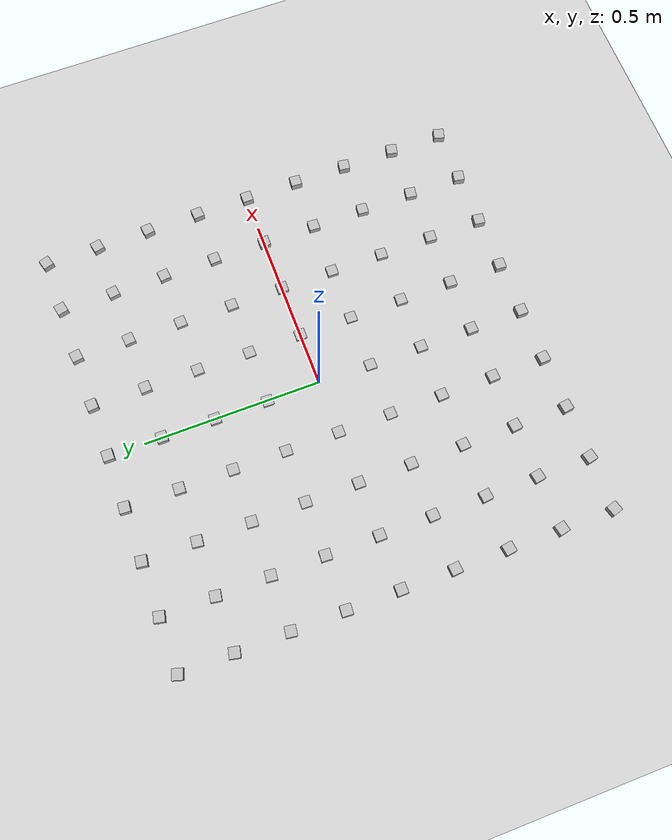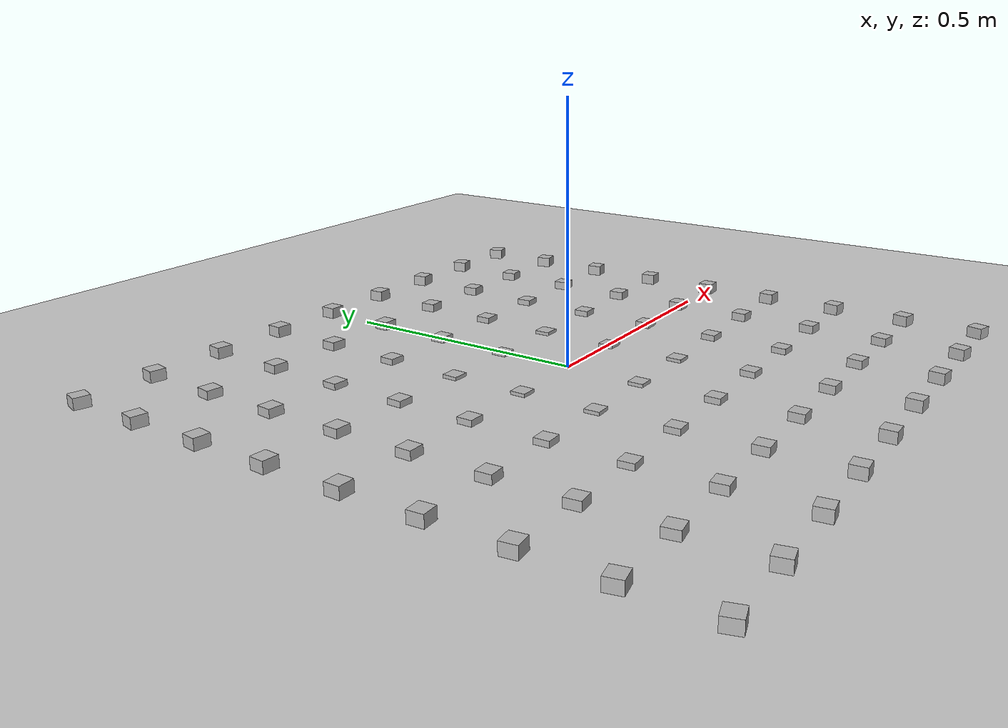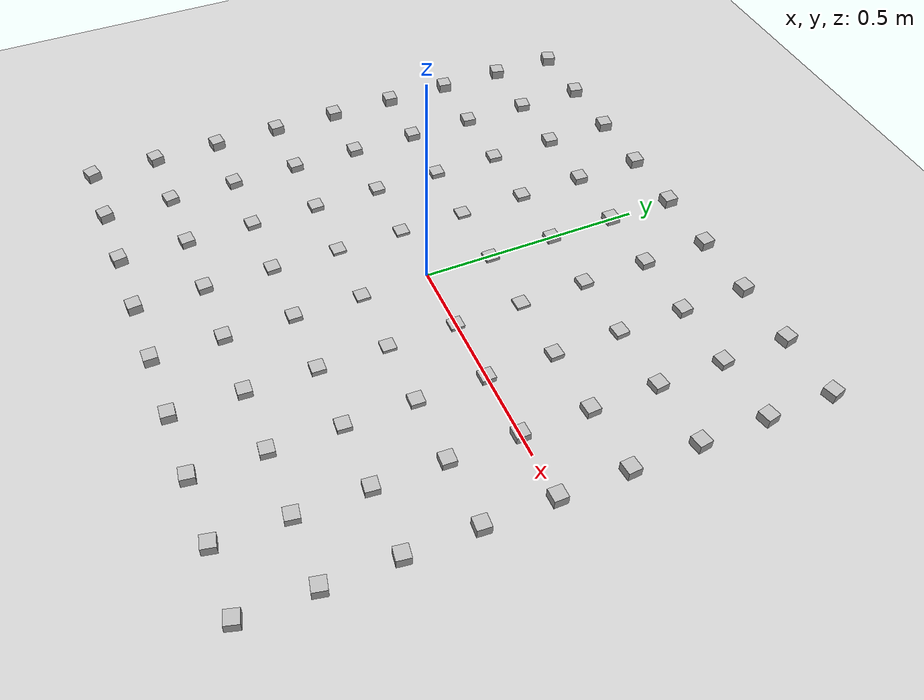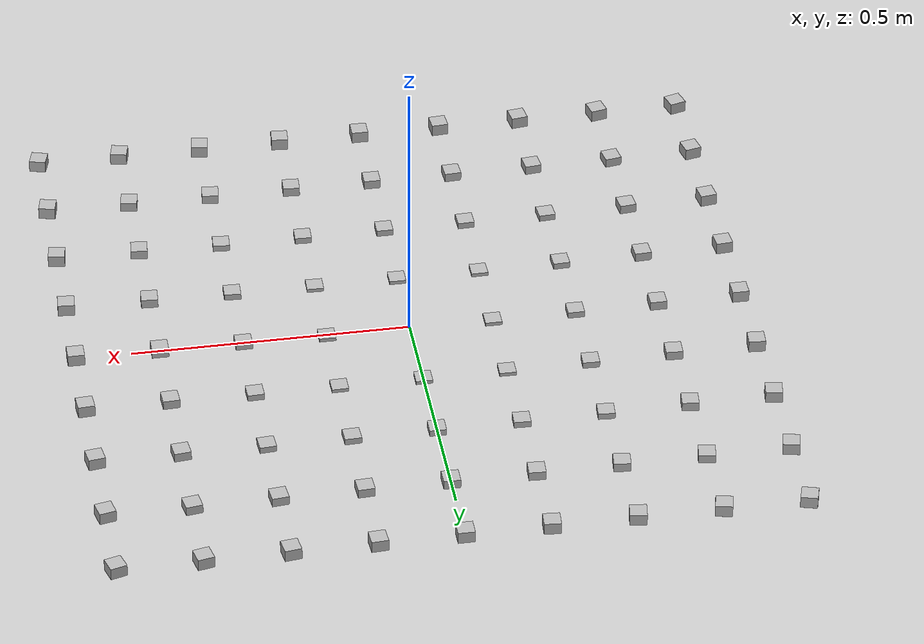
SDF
<?xml version="1.0" ?>
<sdf version="1.5">
  <world name="default">
    <scene>
        <origin_visual>0</origin_visual>
        <grid>0</grid>
    </scene>
    <physics type="ode">
      <max_step_size>0.003</max_step_size>

      <!-- Run as fast as possible -->
      <real_time_update_rate>0.0</real_time_update_rate>
      <ode>
        <constraints>
          <!-- Simulator.cpp -->
          <erp>0.1</erp>
          <cfm>10e-6</cfm>

          <!-- Making this smaller seems to decrease rather than increase stability. -->
          <contact_max_correcting_vel>100</contact_max_correcting_vel>
          <contact_surface_layer>1e-8</contact_surface_layer>
        </constraints>
        <solver>
          <type>world</type>
        </solver>
      </ode>
    </physics>

    <!-- A global light source -->
    <include>
      <uri>model://sun</uri>
    </include>
    <!-- ground plane -->
    <include>
      <uri>model://tol_ground</uri>
    </include>

    <plugin name="tol-control" filename="libtolworldcontrol.so" />

    <!-- insert objects here -->
    <include>
      <uri>model://obstacles</uri>
    </include>

  </world>
</sdf>

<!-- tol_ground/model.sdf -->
<sdf version="1.5">
<!-- Custom ground plane -->
  <model name="tol_ground">
    <static>true</static>
    <link name="link">
      <collision name="collision">
        <geometry>
          <plane>
            <normal>0 0 1</normal>
            <size>100 100</size>
          </plane>
        </geometry>
        <surface>
          <friction>
            <ode>
              <!-- RobogenCollision.cpp -->
              <mu>1</mu>
              <mu2>1</mu2>
              <slip1>0.01</slip1>
              <slip2>0.01</slip2>
            </ode>
          </friction>
          <contact>
            <ode>
              <kd>9.000000e+04</kd>
              <kp>2.000000e+06</kp>
            </ode>
          </contact>
        </surface>
      </collision>
      <visual name="visual">
        <cast_shadows>false</cast_shadows>
        <geometry>
          <plane>
            <normal>0 0 1</normal>
            <size>100 100</size>
          </plane>
        </geometry>
        <material>
          <script>
            <uri>model://tol_ground/materials/scripts</uri>
            <uri>model://tol_ground/materials/textures</uri>
            <name>Floor/Tiles</name>
          </script>
        </material>
      </visual>
    </link>
  </model>
<!-- END Custom ground plane -->
</sdf>

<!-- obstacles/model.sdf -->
<sdf version="1.5"><model name="obstacles"><pose>0.000000e+00 0.000000e+00 0.000000e+00 0.000000e+00 -0.000000e+00 0.000000e+00</pose>
<link name="box"><pose>-6.000000e-01 -6.000000e-01 0.000000e+00 0.000000e+00 -0.000000e+00 2.792527e-01</pose>
<collision name="collision"><pose>0.000000e+00 0.000000e+00 0.000000e+00 0.000000e+00 -0.000000e+00 0.000000e+00</pose>
<geometry><box><size>3.000000e-02 3.000000e-02 4.000000e-02</size></box></geometry></collision>
<visual name="visual"><pose>0.000000e+00 0.000000e+00 0.000000e+00 0.000000e+00 -0.000000e+00 0.000000e+00</pose>
<geometry><box><size>3.000000e-02 3.000000e-02 4.000000e-02</size></box></geometry></visual>
<inertial><mass>1.000000e+00</mass><inertia><ixx>2.083333e-04</ixx><ixy>0.000000e+00</ixy><ixz>0.000000e+00</ixz><iyy>2.083333e-04</iyy><iyz>0.000000e+00</iyz><izz>1.500000e-04</izz></inertia></inertial></link>
<link name="box"><pose>-6.000000e-01 -4.500000e-01 0.000000e+00 0.000000e+00 -0.000000e+00 2.094395e-01</pose>
<collision name="collision"><pose>0.000000e+00 0.000000e+00 0.000000e+00 0.000000e+00 -0.000000e+00 0.000000e+00</pose>
<geometry><box><size>3.000000e-02 3.000000e-02 4.000000e-02</size></box></geometry></collision>
<visual name="visual"><pose>0.000000e+00 0.000000e+00 0.000000e+00 0.000000e+00 -0.000000e+00 0.000000e+00</pose>
<geometry><box><size>3.000000e-02 3.000000e-02 4.000000e-02</size></box></geometry></visual>
<inertial><mass>1.000000e+00</mass><inertia><ixx>2.083333e-04</ixx><ixy>0.000000e+00</ixy><ixz>0.000000e+00</ixz><iyy>2.083333e-04</iyy><iyz>0.000000e+00</iyz><izz>1.500000e-04</izz></inertia></inertial></link>
<link name="box"><pose>-6.000000e-01 -3.000000e-01 0.000000e+00 0.000000e+00 -0.000000e+00 1.396263e-01</pose>
<collision name="collision"><pose>0.000000e+00 0.000000e+00 0.000000e+00 0.000000e+00 -0.000000e+00 0.000000e+00</pose>
<geometry><box><size>3.000000e-02 3.000000e-02 4.000000e-02</size></box></geometry></collision>
<visual name="visual"><pose>0.000000e+00 0.000000e+00 0.000000e+00 0.000000e+00 -0.000000e+00 0.000000e+00</pose>
<geometry><box><size>3.000000e-02 3.000000e-02 4.000000e-02</size></box></geometry></visual>
<inertial><mass>1.000000e+00</mass><inertia><ixx>2.083333e-04</ixx><ixy>0.000000e+00</ixy><ixz>0.000000e+00</ixz><iyy>2.083333e-04</iyy><iyz>0.000000e+00</iyz><izz>1.500000e-04</izz></inertia></inertial></link>
<link name="box"><pose>-6.000000e-01 -1.500000e-01 0.000000e+00 0.000000e+00 -0.000000e+00 6.981317e-02</pose>
<collision name="collision"><pose>0.000000e+00 0.000000e+00 0.000000e+00 0.000000e+00 -0.000000e+00 0.000000e+00</pose>
<geometry><box><size>3.000000e-02 3.000000e-02 4.000000e-02</size></box></geometry></collision>
<visual name="visual"><pose>0.000000e+00 0.000000e+00 0.000000e+00 0.000000e+00 -0.000000e+00 0.000000e+00</pose>
<geometry><box><size>3.000000e-02 3.000000e-02 4.000000e-02</size></box></geometry></visual>
<inertial><mass>1.000000e+00</mass><inertia><ixx>2.083333e-04</ixx><ixy>0.000000e+00</ixy><ixz>0.000000e+00</ixz><iyy>2.083333e-04</iyy><iyz>0.000000e+00</iyz><izz>1.500000e-04</izz></inertia></inertial></link>
<link name="box"><pose>-6.000000e-01 0.000000e+00 0.000000e+00 0.000000e+00 -0.000000e+00 0.000000e+00</pose>
<collision name="collision"><pose>0.000000e+00 0.000000e+00 0.000000e+00 0.000000e+00 -0.000000e+00 0.000000e+00</pose>
<geometry><box><size>3.000000e-02 3.000000e-02 4.000000e-02</size></box></geometry></collision>
<visual name="visual"><pose>0.000000e+00 0.000000e+00 0.000000e+00 0.000000e+00 -0.000000e+00 0.000000e+00</pose>
<geometry><box><size>3.000000e-02 3.000000e-02 4.000000e-02</size></box></geometry></visual>
<inertial><mass>1.000000e+00</mass><inertia><ixx>2.083333e-04</ixx><ixy>0.000000e+00</ixy><ixz>0.000000e+00</ixz><iyy>2.083333e-04</iyy><iyz>0.000000e+00</iyz><izz>1.500000e-04</izz></inertia></inertial></link>
<link name="box"><pose>-6.000000e-01 1.500000e-01 0.000000e+00 0.000000e+00 0.000000e+00 -6.981317e-02</pose>
<collision name="collision"><pose>0.000000e+00 0.000000e+00 0.000000e+00 0.000000e+00 -0.000000e+00 0.000000e+00</pose>
<geometry><box><size>3.000000e-02 3.000000e-02 4.000000e-02</size></box></geometry></collision>
<visual name="visual"><pose>0.000000e+00 0.000000e+00 0.000000e+00 0.000000e+00 -0.000000e+00 0.000000e+00</pose>
<geometry><box><size>3.000000e-02 3.000000e-02 4.000000e-02</size></box></geometry></visual>
<inertial><mass>1.000000e+00</mass><inertia><ixx>2.083333e-04</ixx><ixy>0.000000e+00</ixy><ixz>0.000000e+00</ixz><iyy>2.083333e-04</iyy><iyz>0.000000e+00</iyz><izz>1.500000e-04</izz></inertia></inertial></link>
<link name="box"><pose>-6.000000e-01 3.000000e-01 0.000000e+00 0.000000e+00 0.000000e+00 -1.396263e-01</pose>
<collision name="collision"><pose>0.000000e+00 0.000000e+00 0.000000e+00 0.000000e+00 -0.000000e+00 0.000000e+00</pose>
<geometry><box><size>3.000000e-02 3.000000e-02 4.000000e-02</size></box></geometry></collision>
<visual name="visual"><pose>0.000000e+00 0.000000e+00 0.000000e+00 0.000000e+00 -0.000000e+00 0.000000e+00</pose>
<geometry><box><size>3.000000e-02 3.000000e-02 4.000000e-02</size></box></geometry></visual>
<inertial><mass>1.000000e+00</mass><inertia><ixx>2.083333e-04</ixx><ixy>0.000000e+00</ixy><ixz>0.000000e+00</ixz><iyy>2.083333e-04</iyy><iyz>0.000000e+00</iyz><izz>1.500000e-04</izz></inertia></inertial></link>
<link name="box"><pose>-6.000000e-01 4.500000e-01 0.000000e+00 0.000000e+00 0.000000e+00 -2.094395e-01</pose>
<collision name="collision"><pose>0.000000e+00 0.000000e+00 0.000000e+00 0.000000e+00 -0.000000e+00 0.000000e+00</pose>
<geometry><box><size>3.000000e-02 3.000000e-02 4.000000e-02</size></box></geometry></collision>
<visual name="visual"><pose>0.000000e+00 0.000000e+00 0.000000e+00 0.000000e+00 -0.000000e+00 0.000000e+00</pose>
<geometry><box><size>3.000000e-02 3.000000e-02 4.000000e-02</size></box></geometry></visual>
<inertial><mass>1.000000e+00</mass><inertia><ixx>2.083333e-04</ixx><ixy>0.000000e+00</ixy><ixz>0.000000e+00</ixz><iyy>2.083333e-04</iyy><iyz>0.000000e+00</iyz><izz>1.500000e-04</izz></inertia></inertial></link>
<link name="box"><pose>-6.000000e-01 6.000000e-01 0.000000e+00 0.000000e+00 0.000000e+00 -2.792527e-01</pose>
<collision name="collision"><pose>0.000000e+00 0.000000e+00 0.000000e+00 0.000000e+00 -0.000000e+00 0.000000e+00</pose>
<geometry><box><size>3.000000e-02 3.000000e-02 4.000000e-02</size></box></geometry></collision>
<visual name="visual"><pose>0.000000e+00 0.000000e+00 0.000000e+00 0.000000e+00 -0.000000e+00 0.000000e+00</pose>
<geometry><box><size>3.000000e-02 3.000000e-02 4.000000e-02</size></box></geometry></visual>
<inertial><mass>1.000000e+00</mass><inertia><ixx>2.083333e-04</ixx><ixy>0.000000e+00</ixy><ixz>0.000000e+00</ixz><iyy>2.083333e-04</iyy><iyz>0.000000e+00</iyz><izz>1.500000e-04</izz></inertia></inertial></link>
<link name="box"><pose>-4.500000e-01 -6.000000e-01 0.000000e+00 0.000000e+00 -0.000000e+00 2.094395e-01</pose>
<collision name="collision"><pose>0.000000e+00 0.000000e+00 0.000000e+00 0.000000e+00 -0.000000e+00 0.000000e+00</pose>
<geometry><box><size>3.000000e-02 3.000000e-02 4.000000e-02</size></box></geometry></collision>
<visual name="visual"><pose>0.000000e+00 0.000000e+00 0.000000e+00 0.000000e+00 -0.000000e+00 0.000000e+00</pose>
<geometry><box><size>3.000000e-02 3.000000e-02 4.000000e-02</size></box></geometry></visual>
<inertial><mass>1.000000e+00</mass><inertia><ixx>2.083333e-04</ixx><ixy>0.000000e+00</ixy><ixz>0.000000e+00</ixz><iyy>2.083333e-04</iyy><iyz>0.000000e+00</iyz><izz>1.500000e-04</izz></inertia></inertial></link>
<link name="box"><pose>-4.500000e-01 -4.500000e-01 0.000000e+00 0.000000e+00 -0.000000e+00 1.570796e-01</pose>
<collision name="collision"><pose>0.000000e+00 0.000000e+00 0.000000e+00 0.000000e+00 -0.000000e+00 0.000000e+00</pose>
<geometry><box><size>3.000000e-02 3.000000e-02 3.000000e-02</size></box></geometry></collision>
<visual name="visual"><pose>0.000000e+00 0.000000e+00 0.000000e+00 0.000000e+00 -0.000000e+00 0.000000e+00</pose>
<geometry><box><size>3.000000e-02 3.000000e-02 3.000000e-02</size></box></geometry></visual>
<inertial><mass>1.000000e+00</mass><inertia><ixx>1.500000e-04</ixx><ixy>0.000000e+00</ixy><ixz>0.000000e+00</ixz><iyy>1.500000e-04</iyy><iyz>0.000000e+00</iyz><izz>1.500000e-04</izz></inertia></inertial></link>
<link name="box"><pose>-4.500000e-01 -3.000000e-01 0.000000e+00 0.000000e+00 -0.000000e+00 1.047198e-01</pose>
<collision name="collision"><pose>0.000000e+00 0.000000e+00 0.000000e+00 0.000000e+00 -0.000000e+00 0.000000e+00</pose>
<geometry><box><size>3.000000e-02 3.000000e-02 3.000000e-02</size></box></geometry></collision>
<visual name="visual"><pose>0.000000e+00 0.000000e+00 0.000000e+00 0.000000e+00 -0.000000e+00 0.000000e+00</pose>
<geometry><box><size>3.000000e-02 3.000000e-02 3.000000e-02</size></box></geometry></visual>
<inertial><mass>1.000000e+00</mass><inertia><ixx>1.500000e-04</ixx><ixy>0.000000e+00</ixy><ixz>0.000000e+00</ixz><iyy>1.500000e-04</iyy><iyz>0.000000e+00</iyz><izz>1.500000e-04</izz></inertia></inertial></link>
<link name="box"><pose>-4.500000e-01 -1.500000e-01 0.000000e+00 0.000000e+00 -0.000000e+00 5.235988e-02</pose>
<collision name="collision"><pose>0.000000e+00 0.000000e+00 0.000000e+00 0.000000e+00 -0.000000e+00 0.000000e+00</pose>
<geometry><box><size>3.000000e-02 3.000000e-02 3.000000e-02</size></box></geometry></collision>
<visual name="visual"><pose>0.000000e+00 0.000000e+00 0.000000e+00 0.000000e+00 -0.000000e+00 0.000000e+00</pose>
<geometry><box><size>3.000000e-02 3.000000e-02 3.000000e-02</size></box></geometry></visual>
<inertial><mass>1.000000e+00</mass><inertia><ixx>1.500000e-04</ixx><ixy>0.000000e+00</ixy><ixz>0.000000e+00</ixz><iyy>1.500000e-04</iyy><iyz>0.000000e+00</iyz><izz>1.500000e-04</izz></inertia></inertial></link>
<link name="box"><pose>-4.500000e-01 0.000000e+00 0.000000e+00 0.000000e+00 -0.000000e+00 0.000000e+00</pose>
<collision name="collision"><pose>0.000000e+00 0.000000e+00 0.000000e+00 0.000000e+00 -0.000000e+00 0.000000e+00</pose>
<geometry><box><size>3.000000e-02 3.000000e-02 3.000000e-02</size></box></geometry></collision>
<visual name="visual"><pose>0.000000e+00 0.000000e+00 0.000000e+00 0.000000e+00 -0.000000e+00 0.000000e+00</pose>
<geometry><box><size>3.000000e-02 3.000000e-02 3.000000e-02</size></box></geometry></visual>
<inertial><mass>1.000000e+00</mass><inertia><ixx>1.500000e-04</ixx><ixy>0.000000e+00</ixy><ixz>0.000000e+00</ixz><iyy>1.500000e-04</iyy><iyz>0.000000e+00</iyz><izz>1.500000e-04</izz></inertia></inertial></link>
<link name="box"><pose>-4.500000e-01 1.500000e-01 0.000000e+00 0.000000e+00 0.000000e+00 -5.235988e-02</pose>
<collision name="collision"><pose>0.000000e+00 0.000000e+00 0.000000e+00 0.000000e+00 -0.000000e+00 0.000000e+00</pose>
<geometry><box><size>3.000000e-02 3.000000e-02 3.000000e-02</size></box></geometry></collision>
<visual name="visual"><pose>0.000000e+00 0.000000e+00 0.000000e+00 0.000000e+00 -0.000000e+00 0.000000e+00</pose>
<geometry><box><size>3.000000e-02 3.000000e-02 3.000000e-02</size></box></geometry></visual>
<inertial><mass>1.000000e+00</mass><inertia><ixx>1.500000e-04</ixx><ixy>0.000000e+00</ixy><ixz>0.000000e+00</ixz><iyy>1.500000e-04</iyy><iyz>0.000000e+00</iyz><izz>1.500000e-04</izz></inertia></inertial></link>
<link name="box"><pose>-4.500000e-01 3.000000e-01 0.000000e+00 0.000000e+00 0.000000e+00 -1.047198e-01</pose>
<collision name="collision"><pose>0.000000e+00 0.000000e+00 0.000000e+00 0.000000e+00 -0.000000e+00 0.000000e+00</pose>
<geometry><box><size>3.000000e-02 3.000000e-02 3.000000e-02</size></box></geometry></collision>
<visual name="visual"><pose>0.000000e+00 0.000000e+00 0.000000e+00 0.000000e+00 -0.000000e+00 0.000000e+00</pose>
<geometry><box><size>3.000000e-02 3.000000e-02 3.000000e-02</size></box></geometry></visual>
<inertial><mass>1.000000e+00</mass><inertia><ixx>1.500000e-04</ixx><ixy>0.000000e+00</ixy><ixz>0.000000e+00</ixz><iyy>1.500000e-04</iyy><iyz>0.000000e+00</iyz><izz>1.500000e-04</izz></inertia></inertial></link>
<link name="box"><pose>-4.500000e-01 4.500000e-01 0.000000e+00 0.000000e+00 0.000000e+00 -1.570796e-01</pose>
<collision name="collision"><pose>0.000000e+00 0.000000e+00 0.000000e+00 0.000000e+00 -0.000000e+00 0.000000e+00</pose>
<geometry><box><size>3.000000e-02 3.000000e-02 3.000000e-02</size></box></geometry></collision>
<visual name="visual"><pose>0.000000e+00 0.000000e+00 0.000000e+00 0.000000e+00 -0.000000e+00 0.000000e+00</pose>
<geometry><box><size>3.000000e-02 3.000000e-02 3.000000e-02</size></box></geometry></visual>
<inertial><mass>1.000000e+00</mass><inertia><ixx>1.500000e-04</ixx><ixy>0.000000e+00</ixy><ixz>0.000000e+00</ixz><iyy>1.500000e-04</iyy><iyz>0.000000e+00</iyz><izz>1.500000e-04</izz></inertia></inertial></link>
<link name="box"><pose>-4.500000e-01 6.000000e-01 0.000000e+00 0.000000e+00 0.000000e+00 -2.094395e-01</pose>
<collision name="collision"><pose>0.000000e+00 0.000000e+00 0.000000e+00 0.000000e+00 -0.000000e+00 0.000000e+00</pose>
<geometry><box><size>3.000000e-02 3.000000e-02 4.000000e-02</size></box></geometry></collision>
<visual name="visual"><pose>0.000000e+00 0.000000e+00 0.000000e+00 0.000000e+00 -0.000000e+00 0.000000e+00</pose>
<geometry><box><size>3.000000e-02 3.000000e-02 4.000000e-02</size></box></geometry></visual>
<inertial><mass>1.000000e+00</mass><inertia><ixx>2.083333e-04</ixx><ixy>0.000000e+00</ixy><ixz>0.000000e+00</ixz><iyy>2.083333e-04</iyy><iyz>0.000000e+00</iyz><izz>1.500000e-04</izz></inertia></inertial></link>
<link name="box"><pose>-3.000000e-01 -6.000000e-01 0.000000e+00 0.000000e+00 -0.000000e+00 1.396263e-01</pose>
<collision name="collision"><pose>0.000000e+00 0.000000e+00 0.000000e+00 0.000000e+00 -0.000000e+00 0.000000e+00</pose>
<geometry><box><size>3.000000e-02 3.000000e-02 4.000000e-02</size></box></geometry></collision>
<visual name="visual"><pose>0.000000e+00 0.000000e+00 0.000000e+00 0.000000e+00 -0.000000e+00 0.000000e+00</pose>
<geometry><box><size>3.000000e-02 3.000000e-02 4.000000e-02</size></box></geometry></visual>
<inertial><mass>1.000000e+00</mass><inertia><ixx>2.083333e-04</ixx><ixy>0.000000e+00</ixy><ixz>0.000000e+00</ixz><iyy>2.083333e-04</iyy><iyz>0.000000e+00</iyz><izz>1.500000e-04</izz></inertia></inertial></link>
<link name="box"><pose>-3.000000e-01 -4.500000e-01 0.000000e+00 0.000000e+00 -0.000000e+00 1.047198e-01</pose>
<collision name="collision"><pose>0.000000e+00 0.000000e+00 0.000000e+00 0.000000e+00 -0.000000e+00 0.000000e+00</pose>
<geometry><box><size>3.000000e-02 3.000000e-02 3.000000e-02</size></box></geometry></collision>
<visual name="visual"><pose>0.000000e+00 0.000000e+00 0.000000e+00 0.000000e+00 -0.000000e+00 0.000000e+00</pose>
<geometry><box><size>3.000000e-02 3.000000e-02 3.000000e-02</size></box></geometry></visual>
<inertial><mass>1.000000e+00</mass><inertia><ixx>1.500000e-04</ixx><ixy>0.000000e+00</ixy><ixz>0.000000e+00</ixz><iyy>1.500000e-04</iyy><iyz>0.000000e+00</iyz><izz>1.500000e-04</izz></inertia></inertial></link>
<link name="box"><pose>-3.000000e-01 -3.000000e-01 0.000000e+00 0.000000e+00 -0.000000e+00 6.981317e-02</pose>
<collision name="collision"><pose>0.000000e+00 0.000000e+00 0.000000e+00 0.000000e+00 -0.000000e+00 0.000000e+00</pose>
<geometry><box><size>3.000000e-02 3.000000e-02 2.000000e-02</size></box></geometry></collision>
<visual name="visual"><pose>0.000000e+00 0.000000e+00 0.000000e+00 0.000000e+00 -0.000000e+00 0.000000e+00</pose>
<geometry><box><size>3.000000e-02 3.000000e-02 2.000000e-02</size></box></geometry></visual>
<inertial><mass>1.000000e+00</mass><inertia><ixx>1.083333e-04</ixx><ixy>0.000000e+00</ixy><ixz>0.000000e+00</ixz><iyy>1.083333e-04</iyy><iyz>0.000000e+00</iyz><izz>1.500000e-04</izz></inertia></inertial></link>
<link name="box"><pose>-3.000000e-01 -1.500000e-01 0.000000e+00 0.000000e+00 -0.000000e+00 3.490659e-02</pose>
<collision name="collision"><pose>0.000000e+00 0.000000e+00 0.000000e+00 0.000000e+00 -0.000000e+00 0.000000e+00</pose>
<geometry><box><size>3.000000e-02 3.000000e-02 2.000000e-02</size></box></geometry></collision>
<visual name="visual"><pose>0.000000e+00 0.000000e+00 0.000000e+00 0.000000e+00 -0.000000e+00 0.000000e+00</pose>
<geometry><box><size>3.000000e-02 3.000000e-02 2.000000e-02</size></box></geometry></visual>
<inertial><mass>1.000000e+00</mass><inertia><ixx>1.083333e-04</ixx><ixy>0.000000e+00</ixy><ixz>0.000000e+00</ixz><iyy>1.083333e-04</iyy><iyz>0.000000e+00</iyz><izz>1.500000e-04</izz></inertia></inertial></link>
<link name="box"><pose>-3.000000e-01 0.000000e+00 0.000000e+00 0.000000e+00 -0.000000e+00 0.000000e+00</pose>
<collision name="collision"><pose>0.000000e+00 0.000000e+00 0.000000e+00 0.000000e+00 -0.000000e+00 0.000000e+00</pose>
<geometry><box><size>3.000000e-02 3.000000e-02 2.000000e-02</size></box></geometry></collision>
<visual name="visual"><pose>0.000000e+00 0.000000e+00 0.000000e+00 0.000000e+00 -0.000000e+00 0.000000e+00</pose>
<geometry><box><size>3.000000e-02 3.000000e-02 2.000000e-02</size></box></geometry></visual>
<inertial><mass>1.000000e+00</mass><inertia><ixx>1.083333e-04</ixx><ixy>0.000000e+00</ixy><ixz>0.000000e+00</ixz><iyy>1.083333e-04</iyy><iyz>0.000000e+00</iyz><izz>1.500000e-04</izz></inertia></inertial></link>
<link name="box"><pose>-3.000000e-01 1.500000e-01 0.000000e+00 0.000000e+00 0.000000e+00 -3.490659e-02</pose>
<collision name="collision"><pose>0.000000e+00 0.000000e+00 0.000000e+00 0.000000e+00 -0.000000e+00 0.000000e+00</pose>
<geometry><box><size>3.000000e-02 3.000000e-02 2.000000e-02</size></box></geometry></collision>
<visual name="visual"><pose>0.000000e+00 0.000000e+00 0.000000e+00 0.000000e+00 -0.000000e+00 0.000000e+00</pose>
<geometry><box><size>3.000000e-02 3.000000e-02 2.000000e-02</size></box></geometry></visual>
<inertial><mass>1.000000e+00</mass><inertia><ixx>1.083333e-04</ixx><ixy>0.000000e+00</ixy><ixz>0.000000e+00</ixz><iyy>1.083333e-04</iyy><iyz>0.000000e+00</iyz><izz>1.500000e-04</izz></inertia></inertial></link>
<link name="box"><pose>-3.000000e-01 3.000000e-01 0.000000e+00 0.000000e+00 0.000000e+00 -6.981317e-02</pose>
<collision name="collision"><pose>0.000000e+00 0.000000e+00 0.000000e+00 0.000000e+00 -0.000000e+00 0.000000e+00</pose>
<geometry><box><size>3.000000e-02 3.000000e-02 2.000000e-02</size></box></geometry></collision>
<visual name="visual"><pose>0.000000e+00 0.000000e+00 0.000000e+00 0.000000e+00 -0.000000e+00 0.000000e+00</pose>
<geometry><box><size>3.000000e-02 3.000000e-02 2.000000e-02</size></box></geometry></visual>
<inertial><mass>1.000000e+00</mass><inertia><ixx>1.083333e-04</ixx><ixy>0.000000e+00</ixy><ixz>0.000000e+00</ixz><iyy>1.083333e-04</iyy><iyz>0.000000e+00</iyz><izz>1.500000e-04</izz></inertia></inertial></link>
<link name="box"><pose>-3.000000e-01 4.500000e-01 0.000000e+00 0.000000e+00 0.000000e+00 -1.047198e-01</pose>
<collision name="collision"><pose>0.000000e+00 0.000000e+00 0.000000e+00 0.000000e+00 -0.000000e+00 0.000000e+00</pose>
<geometry><box><size>3.000000e-02 3.000000e-02 3.000000e-02</size></box></geometry></collision>
<visual name="visual"><pose>0.000000e+00 0.000000e+00 0.000000e+00 0.000000e+00 -0.000000e+00 0.000000e+00</pose>
<geometry><box><size>3.000000e-02 3.000000e-02 3.000000e-02</size></box></geometry></visual>
<inertial><mass>1.000000e+00</mass><inertia><ixx>1.500000e-04</ixx><ixy>0.000000e+00</ixy><ixz>0.000000e+00</ixz><iyy>1.500000e-04</iyy><iyz>0.000000e+00</iyz><izz>1.500000e-04</izz></inertia></inertial></link>
<link name="box"><pose>-3.000000e-01 6.000000e-01 0.000000e+00 0.000000e+00 0.000000e+00 -1.396263e-01</pose>
<collision name="collision"><pose>0.000000e+00 0.000000e+00 0.000000e+00 0.000000e+00 -0.000000e+00 0.000000e+00</pose>
<geometry><box><size>3.000000e-02 3.000000e-02 4.000000e-02</size></box></geometry></collision>
<visual name="visual"><pose>0.000000e+00 0.000000e+00 0.000000e+00 0.000000e+00 -0.000000e+00 0.000000e+00</pose>
<geometry><box><size>3.000000e-02 3.000000e-02 4.000000e-02</size></box></geometry></visual>
<inertial><mass>1.000000e+00</mass><inertia><ixx>2.083333e-04</ixx><ixy>0.000000e+00</ixy><ixz>0.000000e+00</ixz><iyy>2.083333e-04</iyy><iyz>0.000000e+00</iyz><izz>1.500000e-04</izz></inertia></inertial></link>
<link name="box"><pose>-1.500000e-01 -6.000000e-01 0.000000e+00 0.000000e+00 -0.000000e+00 6.981317e-02</pose>
<collision name="collision"><pose>0.000000e+00 0.000000e+00 0.000000e+00 0.000000e+00 -0.000000e+00 0.000000e+00</pose>
<geometry><box><size>3.000000e-02 3.000000e-02 4.000000e-02</size></box></geometry></collision>
<visual name="visual"><pose>0.000000e+00 0.000000e+00 0.000000e+00 0.000000e+00 -0.000000e+00 0.000000e+00</pose>
<geometry><box><size>3.000000e-02 3.000000e-02 4.000000e-02</size></box></geometry></visual>
<inertial><mass>1.000000e+00</mass><inertia><ixx>2.083333e-04</ixx><ixy>0.000000e+00</ixy><ixz>0.000000e+00</ixz><iyy>2.083333e-04</iyy><iyz>0.000000e+00</iyz><izz>1.500000e-04</izz></inertia></inertial></link>
<link name="box"><pose>-1.500000e-01 -4.500000e-01 0.000000e+00 0.000000e+00 -0.000000e+00 5.235988e-02</pose>
<collision name="collision"><pose>0.000000e+00 0.000000e+00 0.000000e+00 0.000000e+00 -0.000000e+00 0.000000e+00</pose>
<geometry><box><size>3.000000e-02 3.000000e-02 3.000000e-02</size></box></geometry></collision>
<visual name="visual"><pose>0.000000e+00 0.000000e+00 0.000000e+00 0.000000e+00 -0.000000e+00 0.000000e+00</pose>
<geometry><box><size>3.000000e-02 3.000000e-02 3.000000e-02</size></box></geometry></visual>
<inertial><mass>1.000000e+00</mass><inertia><ixx>1.500000e-04</ixx><ixy>0.000000e+00</ixy><ixz>0.000000e+00</ixz><iyy>1.500000e-04</iyy><iyz>0.000000e+00</iyz><izz>1.500000e-04</izz></inertia></inertial></link>
<link name="box"><pose>-1.500000e-01 -3.000000e-01 0.000000e+00 0.000000e+00 -0.000000e+00 3.490659e-02</pose>
<collision name="collision"><pose>0.000000e+00 0.000000e+00 0.000000e+00 0.000000e+00 -0.000000e+00 0.000000e+00</pose>
<geometry><box><size>3.000000e-02 3.000000e-02 2.000000e-02</size></box></geometry></collision>
<visual name="visual"><pose>0.000000e+00 0.000000e+00 0.000000e+00 0.000000e+00 -0.000000e+00 0.000000e+00</pose>
<geometry><box><size>3.000000e-02 3.000000e-02 2.000000e-02</size></box></geometry></visual>
<inertial><mass>1.000000e+00</mass><inertia><ixx>1.083333e-04</ixx><ixy>0.000000e+00</ixy><ixz>0.000000e+00</ixz><iyy>1.083333e-04</iyy><iyz>0.000000e+00</iyz><izz>1.500000e-04</izz></inertia></inertial></link>
<link name="box"><pose>-1.500000e-01 -1.500000e-01 0.000000e+00 0.000000e+00 -0.000000e+00 1.745329e-02</pose>
<collision name="collision"><pose>0.000000e+00 0.000000e+00 0.000000e+00 0.000000e+00 -0.000000e+00 0.000000e+00</pose>
<geometry><box><size>3.000000e-02 3.000000e-02 1.000000e-02</size></box></geometry></collision>
<visual name="visual"><pose>0.000000e+00 0.000000e+00 0.000000e+00 0.000000e+00 -0.000000e+00 0.000000e+00</pose>
<geometry><box><size>3.000000e-02 3.000000e-02 1.000000e-02</size></box></geometry></visual>
<inertial><mass>1.000000e+00</mass><inertia><ixx>8.333333e-05</ixx><ixy>0.000000e+00</ixy><ixz>0.000000e+00</ixz><iyy>8.333333e-05</iyy><iyz>0.000000e+00</iyz><izz>1.500000e-04</izz></inertia></inertial></link>
<link name="box"><pose>-1.500000e-01 0.000000e+00 0.000000e+00 0.000000e+00 -0.000000e+00 0.000000e+00</pose>
<collision name="collision"><pose>0.000000e+00 0.000000e+00 0.000000e+00 0.000000e+00 -0.000000e+00 0.000000e+00</pose>
<geometry><box><size>3.000000e-02 3.000000e-02 1.000000e-02</size></box></geometry></collision>
<visual name="visual"><pose>0.000000e+00 0.000000e+00 0.000000e+00 0.000000e+00 -0.000000e+00 0.000000e+00</pose>
<geometry><box><size>3.000000e-02 3.000000e-02 1.000000e-02</size></box></geometry></visual>
<inertial><mass>1.000000e+00</mass><inertia><ixx>8.333333e-05</ixx><ixy>0.000000e+00</ixy><ixz>0.000000e+00</ixz><iyy>8.333333e-05</iyy><iyz>0.000000e+00</iyz><izz>1.500000e-04</izz></inertia></inertial></link>
<link name="box"><pose>-1.500000e-01 1.500000e-01 0.000000e+00 0.000000e+00 0.000000e+00 -1.745329e-02</pose>
<collision name="collision"><pose>0.000000e+00 0.000000e+00 0.000000e+00 0.000000e+00 -0.000000e+00 0.000000e+00</pose>
<geometry><box><size>3.000000e-02 3.000000e-02 1.000000e-02</size></box></geometry></collision>
<visual name="visual"><pose>0.000000e+00 0.000000e+00 0.000000e+00 0.000000e+00 -0.000000e+00 0.000000e+00</pose>
<geometry><box><size>3.000000e-02 3.000000e-02 1.000000e-02</size></box></geometry></visual>
<inertial><mass>1.000000e+00</mass><inertia><ixx>8.333333e-05</ixx><ixy>0.000000e+00</ixy><ixz>0.000000e+00</ixz><iyy>8.333333e-05</iyy><iyz>0.000000e+00</iyz><izz>1.500000e-04</izz></inertia></inertial></link>
<link name="box"><pose>-1.500000e-01 3.000000e-01 0.000000e+00 0.000000e+00 0.000000e+00 -3.490659e-02</pose>
<collision name="collision"><pose>0.000000e+00 0.000000e+00 0.000000e+00 0.000000e+00 -0.000000e+00 0.000000e+00</pose>
<geometry><box><size>3.000000e-02 3.000000e-02 2.000000e-02</size></box></geometry></collision>
<visual name="visual"><pose>0.000000e+00 0.000000e+00 0.000000e+00 0.000000e+00 -0.000000e+00 0.000000e+00</pose>
<geometry><box><size>3.000000e-02 3.000000e-02 2.000000e-02</size></box></geometry></visual>
<inertial><mass>1.000000e+00</mass><inertia><ixx>1.083333e-04</ixx><ixy>0.000000e+00</ixy><ixz>0.000000e+00</ixz><iyy>1.083333e-04</iyy><iyz>0.000000e+00</iyz><izz>1.500000e-04</izz></inertia></inertial></link>
<link name="box"><pose>-1.500000e-01 4.500000e-01 0.000000e+00 0.000000e+00 0.000000e+00 -5.235988e-02</pose>
<collision name="collision"><pose>0.000000e+00 0.000000e+00 0.000000e+00 0.000000e+00 -0.000000e+00 0.000000e+00</pose>
<geometry><box><size>3.000000e-02 3.000000e-02 3.000000e-02</size></box></geometry></collision>
<visual name="visual"><pose>0.000000e+00 0.000000e+00 0.000000e+00 0.000000e+00 -0.000000e+00 0.000000e+00</pose>
<geometry><box><size>3.000000e-02 3.000000e-02 3.000000e-02</size></box></geometry></visual>
<inertial><mass>1.000000e+00</mass><inertia><ixx>1.500000e-04</ixx><ixy>0.000000e+00</ixy><ixz>0.000000e+00</ixz><iyy>1.500000e-04</iyy><iyz>0.000000e+00</iyz><izz>1.500000e-04</izz></inertia></inertial></link>
<link name="box"><pose>-1.500000e-01 6.000000e-01 0.000000e+00 0.000000e+00 0.000000e+00 -6.981317e-02</pose>
<collision name="collision"><pose>0.000000e+00 0.000000e+00 0.000000e+00 0.000000e+00 -0.000000e+00 0.000000e+00</pose>
<geometry><box><size>3.000000e-02 3.000000e-02 4.000000e-02</size></box></geometry></collision>
<visual name="visual"><pose>0.000000e+00 0.000000e+00 0.000000e+00 0.000000e+00 -0.000000e+00 0.000000e+00</pose>
<geometry><box><size>3.000000e-02 3.000000e-02 4.000000e-02</size></box></geometry></visual>
<inertial><mass>1.000000e+00</mass><inertia><ixx>2.083333e-04</ixx><ixy>0.000000e+00</ixy><ixz>0.000000e+00</ixz><iyy>2.083333e-04</iyy><iyz>0.000000e+00</iyz><izz>1.500000e-04</izz></inertia></inertial></link>
<link name="box"><pose>0.000000e+00 -6.000000e-01 0.000000e+00 0.000000e+00 -0.000000e+00 0.000000e+00</pose>
<collision name="collision"><pose>0.000000e+00 0.000000e+00 0.000000e+00 0.000000e+00 -0.000000e+00 0.000000e+00</pose>
<geometry><box><size>3.000000e-02 3.000000e-02 4.000000e-02</size></box></geometry></collision>
<visual name="visual"><pose>0.000000e+00 0.000000e+00 0.000000e+00 0.000000e+00 -0.000000e+00 0.000000e+00</pose>
<geometry><box><size>3.000000e-02 3.000000e-02 4.000000e-02</size></box></geometry></visual>
<inertial><mass>1.000000e+00</mass><inertia><ixx>2.083333e-04</ixx><ixy>0.000000e+00</ixy><ixz>0.000000e+00</ixz><iyy>2.083333e-04</iyy><iyz>0.000000e+00</iyz><izz>1.500000e-04</izz></inertia></inertial></link>
<link name="box"><pose>0.000000e+00 -4.500000e-01 0.000000e+00 0.000000e+00 -0.000000e+00 0.000000e+00</pose>
<collision name="collision"><pose>0.000000e+00 0.000000e+00 0.000000e+00 0.000000e+00 -0.000000e+00 0.000000e+00</pose>
<geometry><box><size>3.000000e-02 3.000000e-02 3.000000e-02</size></box></geometry></collision>
<visual name="visual"><pose>0.000000e+00 0.000000e+00 0.000000e+00 0.000000e+00 -0.000000e+00 0.000000e+00</pose>
<geometry><box><size>3.000000e-02 3.000000e-02 3.000000e-02</size></box></geometry></visual>
<inertial><mass>1.000000e+00</mass><inertia><ixx>1.500000e-04</ixx><ixy>0.000000e+00</ixy><ixz>0.000000e+00</ixz><iyy>1.500000e-04</iyy><iyz>0.000000e+00</iyz><izz>1.500000e-04</izz></inertia></inertial></link>
<link name="box"><pose>0.000000e+00 -3.000000e-01 0.000000e+00 0.000000e+00 -0.000000e+00 0.000000e+00</pose>
<collision name="collision"><pose>0.000000e+00 0.000000e+00 0.000000e+00 0.000000e+00 -0.000000e+00 0.000000e+00</pose>
<geometry><box><size>3.000000e-02 3.000000e-02 2.000000e-02</size></box></geometry></collision>
<visual name="visual"><pose>0.000000e+00 0.000000e+00 0.000000e+00 0.000000e+00 -0.000000e+00 0.000000e+00</pose>
<geometry><box><size>3.000000e-02 3.000000e-02 2.000000e-02</size></box></geometry></visual>
<inertial><mass>1.000000e+00</mass><inertia><ixx>1.083333e-04</ixx><ixy>0.000000e+00</ixy><ixz>0.000000e+00</ixz><iyy>1.083333e-04</iyy><iyz>0.000000e+00</iyz><izz>1.500000e-04</izz></inertia></inertial></link>
<link name="box"><pose>0.000000e+00 -1.500000e-01 0.000000e+00 0.000000e+00 -0.000000e+00 0.000000e+00</pose>
<collision name="collision"><pose>0.000000e+00 0.000000e+00 0.000000e+00 0.000000e+00 -0.000000e+00 0.000000e+00</pose>
<geometry><box><size>3.000000e-02 3.000000e-02 1.000000e-02</size></box></geometry></collision>
<visual name="visual"><pose>0.000000e+00 0.000000e+00 0.000000e+00 0.000000e+00 -0.000000e+00 0.000000e+00</pose>
<geometry><box><size>3.000000e-02 3.000000e-02 1.000000e-02</size></box></geometry></visual>
<inertial><mass>1.000000e+00</mass><inertia><ixx>8.333333e-05</ixx><ixy>0.000000e+00</ixy><ixz>0.000000e+00</ixz><iyy>8.333333e-05</iyy><iyz>0.000000e+00</iyz><izz>1.500000e-04</izz></inertia></inertial></link>
<link name="box"><pose>0.000000e+00 0.000000e+00 0.000000e+00 0.000000e+00 -0.000000e+00 0.000000e+00</pose></link>
<link name="box"><pose>0.000000e+00 1.500000e-01 0.000000e+00 0.000000e+00 -0.000000e+00 0.000000e+00</pose>
<collision name="collision"><pose>0.000000e+00 0.000000e+00 0.000000e+00 0.000000e+00 -0.000000e+00 0.000000e+00</pose>
<geometry><box><size>3.000000e-02 3.000000e-02 1.000000e-02</size></box></geometry></collision>
<visual name="visual"><pose>0.000000e+00 0.000000e+00 0.000000e+00 0.000000e+00 -0.000000e+00 0.000000e+00</pose>
<geometry><box><size>3.000000e-02 3.000000e-02 1.000000e-02</size></box></geometry></visual>
<inertial><mass>1.000000e+00</mass><inertia><ixx>8.333333e-05</ixx><ixy>0.000000e+00</ixy><ixz>0.000000e+00</ixz><iyy>8.333333e-05</iyy><iyz>0.000000e+00</iyz><izz>1.500000e-04</izz></inertia></inertial></link>
<link name="box"><pose>0.000000e+00 3.000000e-01 0.000000e+00 0.000000e+00 -0.000000e+00 0.000000e+00</pose>
<collision name="collision"><pose>0.000000e+00 0.000000e+00 0.000000e+00 0.000000e+00 -0.000000e+00 0.000000e+00</pose>
<geometry><box><size>3.000000e-02 3.000000e-02 2.000000e-02</size></box></geometry></collision>
<visual name="visual"><pose>0.000000e+00 0.000000e+00 0.000000e+00 0.000000e+00 -0.000000e+00 0.000000e+00</pose>
<geometry><box><size>3.000000e-02 3.000000e-02 2.000000e-02</size></box></geometry></visual>
<inertial><mass>1.000000e+00</mass><inertia><ixx>1.083333e-04</ixx><ixy>0.000000e+00</ixy><ixz>0.000000e+00</ixz><iyy>1.083333e-04</iyy><iyz>0.000000e+00</iyz><izz>1.500000e-04</izz></inertia></inertial></link>
<link name="box"><pose>0.000000e+00 4.500000e-01 0.000000e+00 0.000000e+00 -0.000000e+00 0.000000e+00</pose>
<collision name="collision"><pose>0.000000e+00 0.000000e+00 0.000000e+00 0.000000e+00 -0.000000e+00 0.000000e+00</pose>
<geometry><box><size>3.000000e-02 3.000000e-02 3.000000e-02</size></box></geometry></collision>
<visual name="visual"><pose>0.000000e+00 0.000000e+00 0.000000e+00 0.000000e+00 -0.000000e+00 0.000000e+00</pose>
<geometry><box><size>3.000000e-02 3.000000e-02 3.000000e-02</size></box></geometry></visual>
<inertial><mass>1.000000e+00</mass><inertia><ixx>1.500000e-04</ixx><ixy>0.000000e+00</ixy><ixz>0.000000e+00</ixz><iyy>1.500000e-04</iyy><iyz>0.000000e+00</iyz><izz>1.500000e-04</izz></inertia></inertial></link>
<link name="box"><pose>0.000000e+00 6.000000e-01 0.000000e+00 0.000000e+00 -0.000000e+00 0.000000e+00</pose>
<collision name="collision"><pose>0.000000e+00 0.000000e+00 0.000000e+00 0.000000e+00 -0.000000e+00 0.000000e+00</pose>
<geometry><box><size>3.000000e-02 3.000000e-02 4.000000e-02</size></box></geometry></collision>
<visual name="visual"><pose>0.000000e+00 0.000000e+00 0.000000e+00 0.000000e+00 -0.000000e+00 0.000000e+00</pose>
<geometry><box><size>3.000000e-02 3.000000e-02 4.000000e-02</size></box></geometry></visual>
<inertial><mass>1.000000e+00</mass><inertia><ixx>2.083333e-04</ixx><ixy>0.000000e+00</ixy><ixz>0.000000e+00</ixz><iyy>2.083333e-04</iyy><iyz>0.000000e+00</iyz><izz>1.500000e-04</izz></inertia></inertial></link>
<link name="box"><pose>1.500000e-01 -6.000000e-01 0.000000e+00 0.000000e+00 0.000000e+00 -6.981317e-02</pose>
<collision name="collision"><pose>0.000000e+00 0.000000e+00 0.000000e+00 0.000000e+00 -0.000000e+00 0.000000e+00</pose>
<geometry><box><size>3.000000e-02 3.000000e-02 4.000000e-02</size></box></geometry></collision>
<visual name="visual"><pose>0.000000e+00 0.000000e+00 0.000000e+00 0.000000e+00 -0.000000e+00 0.000000e+00</pose>
<geometry><box><size>3.000000e-02 3.000000e-02 4.000000e-02</size></box></geometry></visual>
<inertial><mass>1.000000e+00</mass><inertia><ixx>2.083333e-04</ixx><ixy>0.000000e+00</ixy><ixz>0.000000e+00</ixz><iyy>2.083333e-04</iyy><iyz>0.000000e+00</iyz><izz>1.500000e-04</izz></inertia></inertial></link>
<link name="box"><pose>1.500000e-01 -4.500000e-01 0.000000e+00 0.000000e+00 0.000000e+00 -5.235988e-02</pose>
<collision name="collision"><pose>0.000000e+00 0.000000e+00 0.000000e+00 0.000000e+00 -0.000000e+00 0.000000e+00</pose>
<geometry><box><size>3.000000e-02 3.000000e-02 3.000000e-02</size></box></geometry></collision>
<visual name="visual"><pose>0.000000e+00 0.000000e+00 0.000000e+00 0.000000e+00 -0.000000e+00 0.000000e+00</pose>
<geometry><box><size>3.000000e-02 3.000000e-02 3.000000e-02</size></box></geometry></visual>
<inertial><mass>1.000000e+00</mass><inertia><ixx>1.500000e-04</ixx><ixy>0.000000e+00</ixy><ixz>0.000000e+00</ixz><iyy>1.500000e-04</iyy><iyz>0.000000e+00</iyz><izz>1.500000e-04</izz></inertia></inertial></link>
<link name="box"><pose>1.500000e-01 -3.000000e-01 0.000000e+00 0.000000e+00 0.000000e+00 -3.490659e-02</pose>
<collision name="collision"><pose>0.000000e+00 0.000000e+00 0.000000e+00 0.000000e+00 -0.000000e+00 0.000000e+00</pose>
<geometry><box><size>3.000000e-02 3.000000e-02 2.000000e-02</size></box></geometry></collision>
<visual name="visual"><pose>0.000000e+00 0.000000e+00 0.000000e+00 0.000000e+00 -0.000000e+00 0.000000e+00</pose>
<geometry><box><size>3.000000e-02 3.000000e-02 2.000000e-02</size></box></geometry></visual>
<inertial><mass>1.000000e+00</mass><inertia><ixx>1.083333e-04</ixx><ixy>0.000000e+00</ixy><ixz>0.000000e+00</ixz><iyy>1.083333e-04</iyy><iyz>0.000000e+00</iyz><izz>1.500000e-04</izz></inertia></inertial></link>
<link name="box"><pose>1.500000e-01 -1.500000e-01 0.000000e+00 0.000000e+00 0.000000e+00 -1.745329e-02</pose>
<collision name="collision"><pose>0.000000e+00 0.000000e+00 0.000000e+00 0.000000e+00 -0.000000e+00 0.000000e+00</pose>
<geometry><box><size>3.000000e-02 3.000000e-02 1.000000e-02</size></box></geometry></collision>
<visual name="visual"><pose>0.000000e+00 0.000000e+00 0.000000e+00 0.000000e+00 -0.000000e+00 0.000000e+00</pose>
<geometry><box><size>3.000000e-02 3.000000e-02 1.000000e-02</size></box></geometry></visual>
<inertial><mass>1.000000e+00</mass><inertia><ixx>8.333333e-05</ixx><ixy>0.000000e+00</ixy><ixz>0.000000e+00</ixz><iyy>8.333333e-05</iyy><iyz>0.000000e+00</iyz><izz>1.500000e-04</izz></inertia></inertial></link>
<link name="box"><pose>1.500000e-01 0.000000e+00 0.000000e+00 0.000000e+00 -0.000000e+00 0.000000e+00</pose>
<collision name="collision"><pose>0.000000e+00 0.000000e+00 0.000000e+00 0.000000e+00 -0.000000e+00 0.000000e+00</pose>
<geometry><box><size>3.000000e-02 3.000000e-02 1.000000e-02</size></box></geometry></collision>
<visual name="visual"><pose>0.000000e+00 0.000000e+00 0.000000e+00 0.000000e+00 -0.000000e+00 0.000000e+00</pose>
<geometry><box><size>3.000000e-02 3.000000e-02 1.000000e-02</size></box></geometry></visual>
<inertial><mass>1.000000e+00</mass><inertia><ixx>8.333333e-05</ixx><ixy>0.000000e+00</ixy><ixz>0.000000e+00</ixz><iyy>8.333333e-05</iyy><iyz>0.000000e+00</iyz><izz>1.500000e-04</izz></inertia></inertial></link>
<link name="box"><pose>1.500000e-01 1.500000e-01 0.000000e+00 0.000000e+00 -0.000000e+00 1.745329e-02</pose>
<collision name="collision"><pose>0.000000e+00 0.000000e+00 0.000000e+00 0.000000e+00 -0.000000e+00 0.000000e+00</pose>
<geometry><box><size>3.000000e-02 3.000000e-02 1.000000e-02</size></box></geometry></collision>
<visual name="visual"><pose>0.000000e+00 0.000000e+00 0.000000e+00 0.000000e+00 -0.000000e+00 0.000000e+00</pose>
<geometry><box><size>3.000000e-02 3.000000e-02 1.000000e-02</size></box></geometry></visual>
<inertial><mass>1.000000e+00</mass><inertia><ixx>8.333333e-05</ixx><ixy>0.000000e+00</ixy><ixz>0.000000e+00</ixz><iyy>8.333333e-05</iyy><iyz>0.000000e+00</iyz><izz>1.500000e-04</izz></inertia></inertial></link>
<link name="box"><pose>1.500000e-01 3.000000e-01 0.000000e+00 0.000000e+00 -0.000000e+00 3.490659e-02</pose>
<collision name="collision"><pose>0.000000e+00 0.000000e+00 0.000000e+00 0.000000e+00 -0.000000e+00 0.000000e+00</pose>
<geometry><box><size>3.000000e-02 3.000000e-02 2.000000e-02</size></box></geometry></collision>
<visual name="visual"><pose>0.000000e+00 0.000000e+00 0.000000e+00 0.000000e+00 -0.000000e+00 0.000000e+00</pose>
<geometry><box><size>3.000000e-02 3.000000e-02 2.000000e-02</size></box></geometry></visual>
<inertial><mass>1.000000e+00</mass><inertia><ixx>1.083333e-04</ixx><ixy>0.000000e+00</ixy><ixz>0.000000e+00</ixz><iyy>1.083333e-04</iyy><iyz>0.000000e+00</iyz><izz>1.500000e-04</izz></inertia></inertial></link>
<link name="box"><pose>1.500000e-01 4.500000e-01 0.000000e+00 0.000000e+00 -0.000000e+00 5.235988e-02</pose>
<collision name="collision"><pose>0.000000e+00 0.000000e+00 0.000000e+00 0.000000e+00 -0.000000e+00 0.000000e+00</pose>
<geometry><box><size>3.000000e-02 3.000000e-02 3.000000e-02</size></box></geometry></collision>
<visual name="visual"><pose>0.000000e+00 0.000000e+00 0.000000e+00 0.000000e+00 -0.000000e+00 0.000000e+00</pose>
<geometry><box><size>3.000000e-02 3.000000e-02 3.000000e-02</size></box></geometry></visual>
<inertial><mass>1.000000e+00</mass><inertia><ixx>1.500000e-04</ixx><ixy>0.000000e+00</ixy><ixz>0.000000e+00</ixz><iyy>1.500000e-04</iyy><iyz>0.000000e+00</iyz><izz>1.500000e-04</izz></inertia></inertial></link>
<link name="box"><pose>1.500000e-01 6.000000e-01 0.000000e+00 0.000000e+00 -0.000000e+00 6.981317e-02</pose>
<collision name="collision"><pose>0.000000e+00 0.000000e+00 0.000000e+00 0.000000e+00 -0.000000e+00 0.000000e+00</pose>
<geometry><box><size>3.000000e-02 3.000000e-02 4.000000e-02</size></box></geometry></collision>
<visual name="visual"><pose>0.000000e+00 0.000000e+00 0.000000e+00 0.000000e+00 -0.000000e+00 0.000000e+00</pose>
<geometry><box><size>3.000000e-02 3.000000e-02 4.000000e-02</size></box></geometry></visual>
<inertial><mass>1.000000e+00</mass><inertia><ixx>2.083333e-04</ixx><ixy>0.000000e+00</ixy><ixz>0.000000e+00</ixz><iyy>2.083333e-04</iyy><iyz>0.000000e+00</iyz><izz>1.500000e-04</izz></inertia></inertial></link>
<link name="box"><pose>3.000000e-01 -6.000000e-01 0.000000e+00 0.000000e+00 0.000000e+00 -1.396263e-01</pose>
<collision name="collision"><pose>0.000000e+00 0.000000e+00 0.000000e+00 0.000000e+00 -0.000000e+00 0.000000e+00</pose>
<geometry><box><size>3.000000e-02 3.000000e-02 4.000000e-02</size></box></geometry></collision>
<visual name="visual"><pose>0.000000e+00 0.000000e+00 0.000000e+00 0.000000e+00 -0.000000e+00 0.000000e+00</pose>
<geometry><box><size>3.000000e-02 3.000000e-02 4.000000e-02</size></box></geometry></visual>
<inertial><mass>1.000000e+00</mass><inertia><ixx>2.083333e-04</ixx><ixy>0.000000e+00</ixy><ixz>0.000000e+00</ixz><iyy>2.083333e-04</iyy><iyz>0.000000e+00</iyz><izz>1.500000e-04</izz></inertia></inertial></link>
<link name="box"><pose>3.000000e-01 -4.500000e-01 0.000000e+00 0.000000e+00 0.000000e+00 -1.047198e-01</pose>
<collision name="collision"><pose>0.000000e+00 0.000000e+00 0.000000e+00 0.000000e+00 -0.000000e+00 0.000000e+00</pose>
<geometry><box><size>3.000000e-02 3.000000e-02 3.000000e-02</size></box></geometry></collision>
<visual name="visual"><pose>0.000000e+00 0.000000e+00 0.000000e+00 0.000000e+00 -0.000000e+00 0.000000e+00</pose>
<geometry><box><size>3.000000e-02 3.000000e-02 3.000000e-02</size></box></geometry></visual>
<inertial><mass>1.000000e+00</mass><inertia><ixx>1.500000e-04</ixx><ixy>0.000000e+00</ixy><ixz>0.000000e+00</ixz><iyy>1.500000e-04</iyy><iyz>0.000000e+00</iyz><izz>1.500000e-04</izz></inertia></inertial></link>
<link name="box"><pose>3.000000e-01 -3.000000e-01 0.000000e+00 0.000000e+00 0.000000e+00 -6.981317e-02</pose>
<collision name="collision"><pose>0.000000e+00 0.000000e+00 0.000000e+00 0.000000e+00 -0.000000e+00 0.000000e+00</pose>
<geometry><box><size>3.000000e-02 3.000000e-02 2.000000e-02</size></box></geometry></collision>
<visual name="visual"><pose>0.000000e+00 0.000000e+00 0.000000e+00 0.000000e+00 -0.000000e+00 0.000000e+00</pose>
<geometry><box><size>3.000000e-02 3.000000e-02 2.000000e-02</size></box></geometry></visual>
<inertial><mass>1.000000e+00</mass><inertia><ixx>1.083333e-04</ixx><ixy>0.000000e+00</ixy><ixz>0.000000e+00</ixz><iyy>1.083333e-04</iyy><iyz>0.000000e+00</iyz><izz>1.500000e-04</izz></inertia></inertial></link>
<link name="box"><pose>3.000000e-01 -1.500000e-01 0.000000e+00 0.000000e+00 0.000000e+00 -3.490659e-02</pose>
<collision name="collision"><pose>0.000000e+00 0.000000e+00 0.000000e+00 0.000000e+00 -0.000000e+00 0.000000e+00</pose>
<geometry><box><size>3.000000e-02 3.000000e-02 2.000000e-02</size></box></geometry></collision>
<visual name="visual"><pose>0.000000e+00 0.000000e+00 0.000000e+00 0.000000e+00 -0.000000e+00 0.000000e+00</pose>
<geometry><box><size>3.000000e-02 3.000000e-02 2.000000e-02</size></box></geometry></visual>
<inertial><mass>1.000000e+00</mass><inertia><ixx>1.083333e-04</ixx><ixy>0.000000e+00</ixy><ixz>0.000000e+00</ixz><iyy>1.083333e-04</iyy><iyz>0.000000e+00</iyz><izz>1.500000e-04</izz></inertia></inertial></link>
<link name="box"><pose>3.000000e-01 0.000000e+00 0.000000e+00 0.000000e+00 -0.000000e+00 0.000000e+00</pose>
<collision name="collision"><pose>0.000000e+00 0.000000e+00 0.000000e+00 0.000000e+00 -0.000000e+00 0.000000e+00</pose>
<geometry><box><size>3.000000e-02 3.000000e-02 2.000000e-02</size></box></geometry></collision>
<visual name="visual"><pose>0.000000e+00 0.000000e+00 0.000000e+00 0.000000e+00 -0.000000e+00 0.000000e+00</pose>
<geometry><box><size>3.000000e-02 3.000000e-02 2.000000e-02</size></box></geometry></visual>
<inertial><mass>1.000000e+00</mass><inertia><ixx>1.083333e-04</ixx><ixy>0.000000e+00</ixy><ixz>0.000000e+00</ixz><iyy>1.083333e-04</iyy><iyz>0.000000e+00</iyz><izz>1.500000e-04</izz></inertia></inertial></link>
<link name="box"><pose>3.000000e-01 1.500000e-01 0.000000e+00 0.000000e+00 -0.000000e+00 3.490659e-02</pose>
<collision name="collision"><pose>0.000000e+00 0.000000e+00 0.000000e+00 0.000000e+00 -0.000000e+00 0.000000e+00</pose>
<geometry><box><size>3.000000e-02 3.000000e-02 2.000000e-02</size></box></geometry></collision>
<visual name="visual"><pose>0.000000e+00 0.000000e+00 0.000000e+00 0.000000e+00 -0.000000e+00 0.000000e+00</pose>
<geometry><box><size>3.000000e-02 3.000000e-02 2.000000e-02</size></box></geometry></visual>
<inertial><mass>1.000000e+00</mass><inertia><ixx>1.083333e-04</ixx><ixy>0.000000e+00</ixy><ixz>0.000000e+00</ixz><iyy>1.083333e-04</iyy><iyz>0.000000e+00</iyz><izz>1.500000e-04</izz></inertia></inertial></link>
<link name="box"><pose>3.000000e-01 3.000000e-01 0.000000e+00 0.000000e+00 -0.000000e+00 6.981317e-02</pose>
<collision name="collision"><pose>0.000000e+00 0.000000e+00 0.000000e+00 0.000000e+00 -0.000000e+00 0.000000e+00</pose>
<geometry><box><size>3.000000e-02 3.000000e-02 2.000000e-02</size></box></geometry></collision>
<visual name="visual"><pose>0.000000e+00 0.000000e+00 0.000000e+00 0.000000e+00 -0.000000e+00 0.000000e+00</pose>
<geometry><box><size>3.000000e-02 3.000000e-02 2.000000e-02</size></box></geometry></visual>
<inertial><mass>1.000000e+00</mass><inertia><ixx>1.083333e-04</ixx><ixy>0.000000e+00</ixy><ixz>0.000000e+00</ixz><iyy>1.083333e-04</iyy><iyz>0.000000e+00</iyz><izz>1.500000e-04</izz></inertia></inertial></link>
<link name="box"><pose>3.000000e-01 4.500000e-01 0.000000e+00 0.000000e+00 -0.000000e+00 1.047198e-01</pose>
<collision name="collision"><pose>0.000000e+00 0.000000e+00 0.000000e+00 0.000000e+00 -0.000000e+00 0.000000e+00</pose>
<geometry><box><size>3.000000e-02 3.000000e-02 3.000000e-02</size></box></geometry></collision>
<visual name="visual"><pose>0.000000e+00 0.000000e+00 0.000000e+00 0.000000e+00 -0.000000e+00 0.000000e+00</pose>
<geometry><box><size>3.000000e-02 3.000000e-02 3.000000e-02</size></box></geometry></visual>
<inertial><mass>1.000000e+00</mass><inertia><ixx>1.500000e-04</ixx><ixy>0.000000e+00</ixy><ixz>0.000000e+00</ixz><iyy>1.500000e-04</iyy><iyz>0.000000e+00</iyz><izz>1.500000e-04</izz></inertia></inertial></link>
<link name="box"><pose>3.000000e-01 6.000000e-01 0.000000e+00 0.000000e+00 -0.000000e+00 1.396263e-01</pose>
<collision name="collision"><pose>0.000000e+00 0.000000e+00 0.000000e+00 0.000000e+00 -0.000000e+00 0.000000e+00</pose>
<geometry><box><size>3.000000e-02 3.000000e-02 4.000000e-02</size></box></geometry></collision>
<visual name="visual"><pose>0.000000e+00 0.000000e+00 0.000000e+00 0.000000e+00 -0.000000e+00 0.000000e+00</pose>
<geometry><box><size>3.000000e-02 3.000000e-02 4.000000e-02</size></box></geometry></visual>
<inertial><mass>1.000000e+00</mass><inertia><ixx>2.083333e-04</ixx><ixy>0.000000e+00</ixy><ixz>0.000000e+00</ixz><iyy>2.083333e-04</iyy><iyz>0.000000e+00</iyz><izz>1.500000e-04</izz></inertia></inertial></link>
<link name="box"><pose>4.500000e-01 -6.000000e-01 0.000000e+00 0.000000e+00 0.000000e+00 -2.094395e-01</pose>
<collision name="collision"><pose>0.000000e+00 0.000000e+00 0.000000e+00 0.000000e+00 -0.000000e+00 0.000000e+00</pose>
<geometry><box><size>3.000000e-02 3.000000e-02 4.000000e-02</size></box></geometry></collision>
<visual name="visual"><pose>0.000000e+00 0.000000e+00 0.000000e+00 0.000000e+00 -0.000000e+00 0.000000e+00</pose>
<geometry><box><size>3.000000e-02 3.000000e-02 4.000000e-02</size></box></geometry></visual>
<inertial><mass>1.000000e+00</mass><inertia><ixx>2.083333e-04</ixx><ixy>0.000000e+00</ixy><ixz>0.000000e+00</ixz><iyy>2.083333e-04</iyy><iyz>0.000000e+00</iyz><izz>1.500000e-04</izz></inertia></inertial></link>
<link name="box"><pose>4.500000e-01 -4.500000e-01 0.000000e+00 0.000000e+00 0.000000e+00 -1.570796e-01</pose>
<collision name="collision"><pose>0.000000e+00 0.000000e+00 0.000000e+00 0.000000e+00 -0.000000e+00 0.000000e+00</pose>
<geometry><box><size>3.000000e-02 3.000000e-02 3.000000e-02</size></box></geometry></collision>
<visual name="visual"><pose>0.000000e+00 0.000000e+00 0.000000e+00 0.000000e+00 -0.000000e+00 0.000000e+00</pose>
<geometry><box><size>3.000000e-02 3.000000e-02 3.000000e-02</size></box></geometry></visual>
<inertial><mass>1.000000e+00</mass><inertia><ixx>1.500000e-04</ixx><ixy>0.000000e+00</ixy><ixz>0.000000e+00</ixz><iyy>1.500000e-04</iyy><iyz>0.000000e+00</iyz><izz>1.500000e-04</izz></inertia></inertial></link>
<link name="box"><pose>4.500000e-01 -3.000000e-01 0.000000e+00 0.000000e+00 0.000000e+00 -1.047198e-01</pose>
<collision name="collision"><pose>0.000000e+00 0.000000e+00 0.000000e+00 0.000000e+00 -0.000000e+00 0.000000e+00</pose>
<geometry><box><size>3.000000e-02 3.000000e-02 3.000000e-02</size></box></geometry></collision>
<visual name="visual"><pose>0.000000e+00 0.000000e+00 0.000000e+00 0.000000e+00 -0.000000e+00 0.000000e+00</pose>
<geometry><box><size>3.000000e-02 3.000000e-02 3.000000e-02</size></box></geometry></visual>
<inertial><mass>1.000000e+00</mass><inertia><ixx>1.500000e-04</ixx><ixy>0.000000e+00</ixy><ixz>0.000000e+00</ixz><iyy>1.500000e-04</iyy><iyz>0.000000e+00</iyz><izz>1.500000e-04</izz></inertia></inertial></link>
<link name="box"><pose>4.500000e-01 -1.500000e-01 0.000000e+00 0.000000e+00 0.000000e+00 -5.235988e-02</pose>
<collision name="collision"><pose>0.000000e+00 0.000000e+00 0.000000e+00 0.000000e+00 -0.000000e+00 0.000000e+00</pose>
<geometry><box><size>3.000000e-02 3.000000e-02 3.000000e-02</size></box></geometry></collision>
<visual name="visual"><pose>0.000000e+00 0.000000e+00 0.000000e+00 0.000000e+00 -0.000000e+00 0.000000e+00</pose>
<geometry><box><size>3.000000e-02 3.000000e-02 3.000000e-02</size></box></geometry></visual>
<inertial><mass>1.000000e+00</mass><inertia><ixx>1.500000e-04</ixx><ixy>0.000000e+00</ixy><ixz>0.000000e+00</ixz><iyy>1.500000e-04</iyy><iyz>0.000000e+00</iyz><izz>1.500000e-04</izz></inertia></inertial></link>
<link name="box"><pose>4.500000e-01 0.000000e+00 0.000000e+00 0.000000e+00 -0.000000e+00 0.000000e+00</pose>
<collision name="collision"><pose>0.000000e+00 0.000000e+00 0.000000e+00 0.000000e+00 -0.000000e+00 0.000000e+00</pose>
<geometry><box><size>3.000000e-02 3.000000e-02 3.000000e-02</size></box></geometry></collision>
<visual name="visual"><pose>0.000000e+00 0.000000e+00 0.000000e+00 0.000000e+00 -0.000000e+00 0.000000e+00</pose>
<geometry><box><size>3.000000e-02 3.000000e-02 3.000000e-02</size></box></geometry></visual>
<inertial><mass>1.000000e+00</mass><inertia><ixx>1.500000e-04</ixx><ixy>0.000000e+00</ixy><ixz>0.000000e+00</ixz><iyy>1.500000e-04</iyy><iyz>0.000000e+00</iyz><izz>1.500000e-04</izz></inertia></inertial></link>
<link name="box"><pose>4.500000e-01 1.500000e-01 0.000000e+00 0.000000e+00 -0.000000e+00 5.235988e-02</pose>
<collision name="collision"><pose>0.000000e+00 0.000000e+00 0.000000e+00 0.000000e+00 -0.000000e+00 0.000000e+00</pose>
<geometry><box><size>3.000000e-02 3.000000e-02 3.000000e-02</size></box></geometry></collision>
<visual name="visual"><pose>0.000000e+00 0.000000e+00 0.000000e+00 0.000000e+00 -0.000000e+00 0.000000e+00</pose>
<geometry><box><size>3.000000e-02 3.000000e-02 3.000000e-02</size></box></geometry></visual>
<inertial><mass>1.000000e+00</mass><inertia><ixx>1.500000e-04</ixx><ixy>0.000000e+00</ixy><ixz>0.000000e+00</ixz><iyy>1.500000e-04</iyy><iyz>0.000000e+00</iyz><izz>1.500000e-04</izz></inertia></inertial></link>
<link name="box"><pose>4.500000e-01 3.000000e-01 0.000000e+00 0.000000e+00 -0.000000e+00 1.047198e-01</pose>
<collision name="collision"><pose>0.000000e+00 0.000000e+00 0.000000e+00 0.000000e+00 -0.000000e+00 0.000000e+00</pose>
<geometry><box><size>3.000000e-02 3.000000e-02 3.000000e-02</size></box></geometry></collision>
<visual name="visual"><pose>0.000000e+00 0.000000e+00 0.000000e+00 0.000000e+00 -0.000000e+00 0.000000e+00</pose>
<geometry><box><size>3.000000e-02 3.000000e-02 3.000000e-02</size></box></geometry></visual>
<inertial><mass>1.000000e+00</mass><inertia><ixx>1.500000e-04</ixx><ixy>0.000000e+00</ixy><ixz>0.000000e+00</ixz><iyy>1.500000e-04</iyy><iyz>0.000000e+00</iyz><izz>1.500000e-04</izz></inertia></inertial></link>
<link name="box"><pose>4.500000e-01 4.500000e-01 0.000000e+00 0.000000e+00 -0.000000e+00 1.570796e-01</pose>
<collision name="collision"><pose>0.000000e+00 0.000000e+00 0.000000e+00 0.000000e+00 -0.000000e+00 0.000000e+00</pose>
<geometry><box><size>3.000000e-02 3.000000e-02 3.000000e-02</size></box></geometry></collision>
<visual name="visual"><pose>0.000000e+00 0.000000e+00 0.000000e+00 0.000000e+00 -0.000000e+00 0.000000e+00</pose>
<geometry><box><size>3.000000e-02 3.000000e-02 3.000000e-02</size></box></geometry></visual>
<inertial><mass>1.000000e+00</mass><inertia><ixx>1.500000e-04</ixx><ixy>0.000000e+00</ixy><ixz>0.000000e+00</ixz><iyy>1.500000e-04</iyy><iyz>0.000000e+00</iyz><izz>1.500000e-04</izz></inertia></inertial></link>
<link name="box"><pose>4.500000e-01 6.000000e-01 0.000000e+00 0.000000e+00 -0.000000e+00 2.094395e-01</pose>
<collision name="collision"><pose>0.000000e+00 0.000000e+00 0.000000e+00 0.000000e+00 -0.000000e+00 0.000000e+00</pose>
<geometry><box><size>3.000000e-02 3.000000e-02 4.000000e-02</size></box></geometry></collision>
<visual name="visual"><pose>0.000000e+00 0.000000e+00 0.000000e+00 0.000000e+00 -0.000000e+00 0.000000e+00</pose>
<geometry><box><size>3.000000e-02 3.000000e-02 4.000000e-02</size></box></geometry></visual>
<inertial><mass>1.000000e+00</mass><inertia><ixx>2.083333e-04</ixx><ixy>0.000000e+00</ixy><ixz>0.000000e+00</ixz><iyy>2.083333e-04</iyy><iyz>0.000000e+00</iyz><izz>1.500000e-04</izz></inertia></inertial></link>
<link name="box"><pose>6.000000e-01 -6.000000e-01 0.000000e+00 0.000000e+00 0.000000e+00 -2.792527e-01</pose>
<collision name="collision"><pose>0.000000e+00 0.000000e+00 0.000000e+00 0.000000e+00 -0.000000e+00 0.000000e+00</pose>
<geometry><box><size>3.000000e-02 3.000000e-02 4.000000e-02</size></box></geometry></collision>
<visual name="visual"><pose>0.000000e+00 0.000000e+00 0.000000e+00 0.000000e+00 -0.000000e+00 0.000000e+00</pose>
<geometry><box><size>3.000000e-02 3.000000e-02 4.000000e-02</size></box></geometry></visual>
<inertial><mass>1.000000e+00</mass><inertia><ixx>2.083333e-04</ixx><ixy>0.000000e+00</ixy><ixz>0.000000e+00</ixz><iyy>2.083333e-04</iyy><iyz>0.000000e+00</iyz><izz>1.500000e-04</izz></inertia></inertial></link>
<link name="box"><pose>6.000000e-01 -4.500000e-01 0.000000e+00 0.000000e+00 0.000000e+00 -2.094395e-01</pose>
<collision name="collision"><pose>0.000000e+00 0.000000e+00 0.000000e+00 0.000000e+00 -0.000000e+00 0.000000e+00</pose>
<geometry><box><size>3.000000e-02 3.000000e-02 4.000000e-02</size></box></geometry></collision>
<visual name="visual"><pose>0.000000e+00 0.000000e+00 0.000000e+00 0.000000e+00 -0.000000e+00 0.000000e+00</pose>
<geometry><box><size>3.000000e-02 3.000000e-02 4.000000e-02</size></box></geometry></visual>
<inertial><mass>1.000000e+00</mass><inertia><ixx>2.083333e-04</ixx><ixy>0.000000e+00</ixy><ixz>0.000000e+00</ixz><iyy>2.083333e-04</iyy><iyz>0.000000e+00</iyz><izz>1.500000e-04</izz></inertia></inertial></link>
<link name="box"><pose>6.000000e-01 -3.000000e-01 0.000000e+00 0.000000e+00 0.000000e+00 -1.396263e-01</pose>
<collision name="collision"><pose>0.000000e+00 0.000000e+00 0.000000e+00 0.000000e+00 -0.000000e+00 0.000000e+00</pose>
<geometry><box><size>3.000000e-02 3.000000e-02 4.000000e-02</size></box></geometry></collision>
<visual name="visual"><pose>0.000000e+00 0.000000e+00 0.000000e+00 0.000000e+00 -0.000000e+00 0.000000e+00</pose>
<geometry><box><size>3.000000e-02 3.000000e-02 4.000000e-02</size></box></geometry></visual>
<inertial><mass>1.000000e+00</mass><inertia><ixx>2.083333e-04</ixx><ixy>0.000000e+00</ixy><ixz>0.000000e+00</ixz><iyy>2.083333e-04</iyy><iyz>0.000000e+00</iyz><izz>1.500000e-04</izz></inertia></inertial></link>
<link name="box"><pose>6.000000e-01 -1.500000e-01 0.000000e+00 0.000000e+00 0.000000e+00 -6.981317e-02</pose>
<collision name="collision"><pose>0.000000e+00 0.000000e+00 0.000000e+00 0.000000e+00 -0.000000e+00 0.000000e+00</pose>
<geometry><box><size>3.000000e-02 3.000000e-02 4.000000e-02</size></box></geometry></collision>
<visual name="visual"><pose>0.000000e+00 0.000000e+00 0.000000e+00 0.000000e+00 -0.000000e+00 0.000000e+00</pose>
<geometry><box><size>3.000000e-02 3.000000e-02 4.000000e-02</size></box></geometry></visual>
<inertial><mass>1.000000e+00</mass><inertia><ixx>2.083333e-04</ixx><ixy>0.000000e+00</ixy><ixz>0.000000e+00</ixz><iyy>2.083333e-04</iyy><iyz>0.000000e+00</iyz><izz>1.500000e-04</izz></inertia></inertial></link>
<link name="box"><pose>6.000000e-01 0.000000e+00 0.000000e+00 0.000000e+00 -0.000000e+00 0.000000e+00</pose>
<collision name="collision"><pose>0.000000e+00 0.000000e+00 0.000000e+00 0.000000e+00 -0.000000e+00 0.000000e+00</pose>
<geometry><box><size>3.000000e-02 3.000000e-02 4.000000e-02</size></box></geometry></collision>
<visual name="visual"><pose>0.000000e+00 0.000000e+00 0.000000e+00 0.000000e+00 -0.000000e+00 0.000000e+00</pose>
<geometry><box><size>3.000000e-02 3.000000e-02 4.000000e-02</size></box></geometry></visual>
<inertial><mass>1.000000e+00</mass><inertia><ixx>2.083333e-04</ixx><ixy>0.000000e+00</ixy><ixz>0.000000e+00</ixz><iyy>2.083333e-04</iyy><iyz>0.000000e+00</iyz><izz>1.500000e-04</izz></inertia></inertial></link>
<link name="box"><pose>6.000000e-01 1.500000e-01 0.000000e+00 0.000000e+00 -0.000000e+00 6.981317e-02</pose>
<collision name="collision"><pose>0.000000e+00 0.000000e+00 0.000000e+00 0.000000e+00 -0.000000e+00 0.000000e+00</pose>
<geometry><box><size>3.000000e-02 3.000000e-02 4.000000e-02</size></box></geometry></collision>
<visual name="visual"><pose>0.000000e+00 0.000000e+00 0.000000e+00 0.000000e+00 -0.000000e+00 0.000000e+00</pose>
<geometry><box><size>3.000000e-02 3.000000e-02 4.000000e-02</size></box></geometry></visual>
<inertial><mass>1.000000e+00</mass><inertia><ixx>2.083333e-04</ixx><ixy>0.000000e+00</ixy><ixz>0.000000e+00</ixz><iyy>2.083333e-04</iyy><iyz>0.000000e+00</iyz><izz>1.500000e-04</izz></inertia></inertial></link>
<link name="box"><pose>6.000000e-01 3.000000e-01 0.000000e+00 0.000000e+00 -0.000000e+00 1.396263e-01</pose>
<collision name="collision"><pose>0.000000e+00 0.000000e+00 0.000000e+00 0.000000e+00 -0.000000e+00 0.000000e+00</pose>
<geometry><box><size>3.000000e-02 3.000000e-02 4.000000e-02</size></box></geometry></collision>
<visual name="visual"><pose>0.000000e+00 0.000000e+00 0.000000e+00 0.000000e+00 -0.000000e+00 0.000000e+00</pose>
<geometry><box><size>3.000000e-02 3.000000e-02 4.000000e-02</size></box></geometry></visual>
<inertial><mass>1.000000e+00</mass><inertia><ixx>2.083333e-04</ixx><ixy>0.000000e+00</ixy><ixz>0.000000e+00</ixz><iyy>2.083333e-04</iyy><iyz>0.000000e+00</iyz><izz>1.500000e-04</izz></inertia></inertial></link>
<link name="box"><pose>6.000000e-01 4.500000e-01 0.000000e+00 0.000000e+00 -0.000000e+00 2.094395e-01</pose>
<collision name="collision"><pose>0.000000e+00 0.000000e+00 0.000000e+00 0.000000e+00 -0.000000e+00 0.000000e+00</pose>
<geometry><box><size>3.000000e-02 3.000000e-02 4.000000e-02</size></box></geometry></collision>
<visual name="visual"><pose>0.000000e+00 0.000000e+00 0.000000e+00 0.000000e+00 -0.000000e+00 0.000000e+00</pose>
<geometry><box><size>3.000000e-02 3.000000e-02 4.000000e-02</size></box></geometry></visual>
<inertial><mass>1.000000e+00</mass><inertia><ixx>2.083333e-04</ixx><ixy>0.000000e+00</ixy><ixz>0.000000e+00</ixz><iyy>2.083333e-04</iyy><iyz>0.000000e+00</iyz><izz>1.500000e-04</izz></inertia></inertial></link>
<link name="box"><pose>6.000000e-01 6.000000e-01 0.000000e+00 0.000000e+00 -0.000000e+00 2.792527e-01</pose>
<collision name="collision"><pose>0.000000e+00 0.000000e+00 0.000000e+00 0.000000e+00 -0.000000e+00 0.000000e+00</pose>
<geometry><box><size>3.000000e-02 3.000000e-02 4.000000e-02</size></box></geometry></collision>
<visual name="visual"><pose>0.000000e+00 0.000000e+00 0.000000e+00 0.000000e+00 -0.000000e+00 0.000000e+00</pose>
<geometry><box><size>3.000000e-02 3.000000e-02 4.000000e-02</size></box></geometry></visual>
<inertial><mass>1.000000e+00</mass><inertia><ixx>2.083333e-04</ixx><ixy>0.000000e+00</ixy><ixz>0.000000e+00</ixz><iyy>2.083333e-04</iyy><iyz>0.000000e+00</iyz><izz>1.500000e-04</izz></inertia></inertial></link>
<static>1</static></model></sdf>
